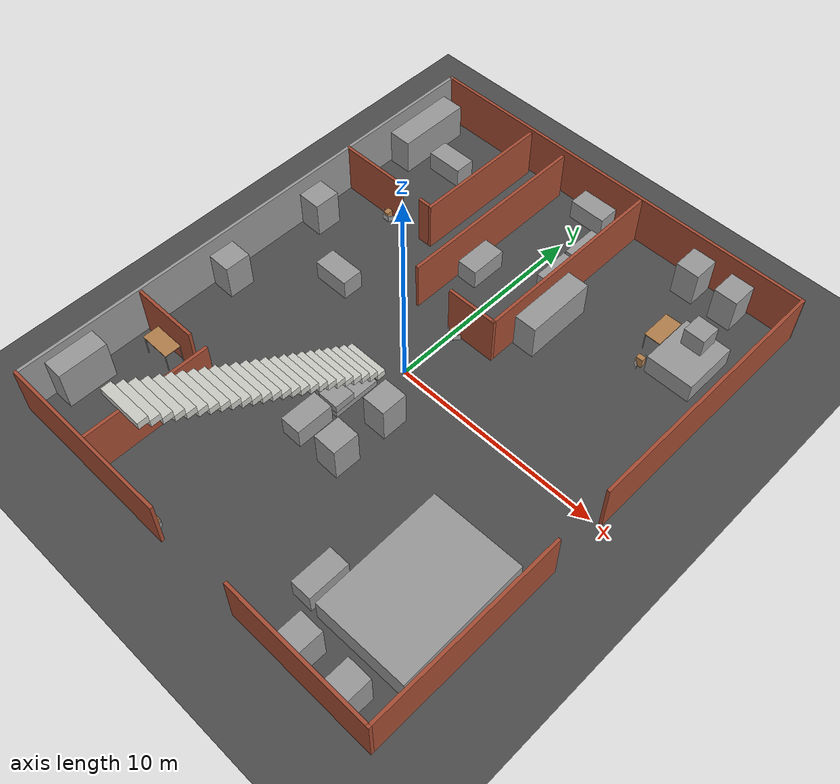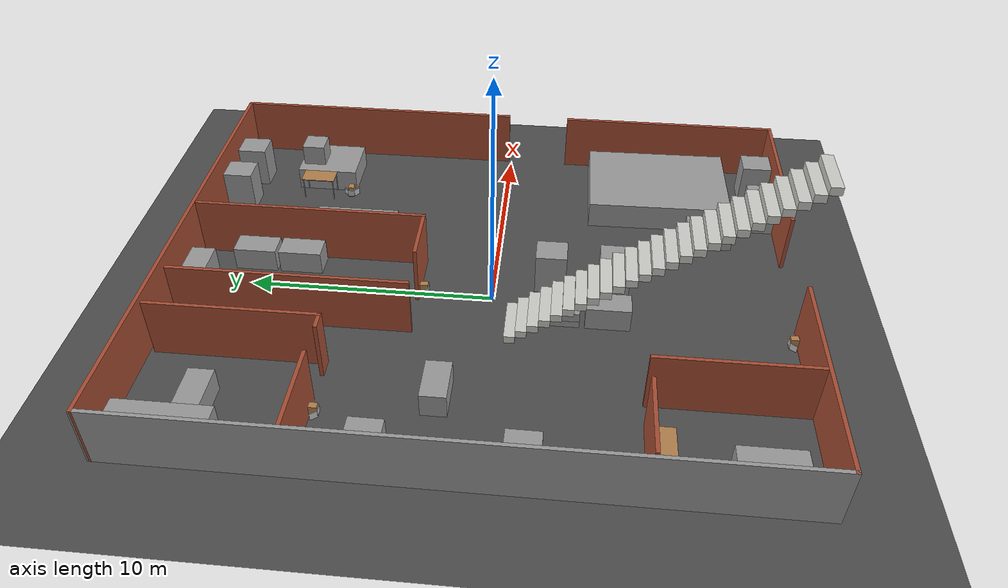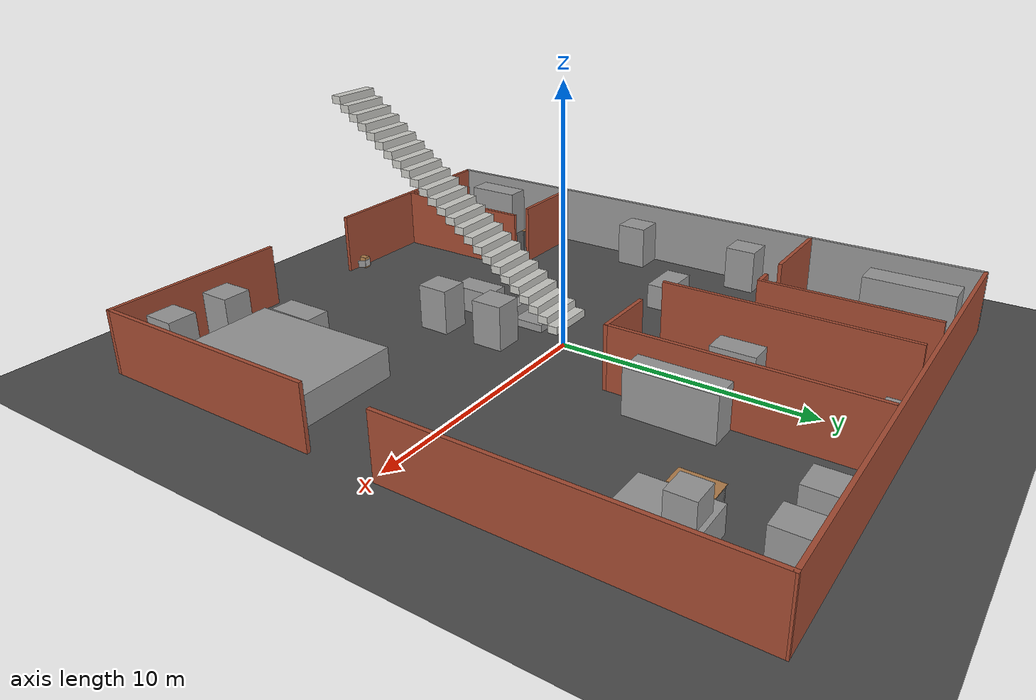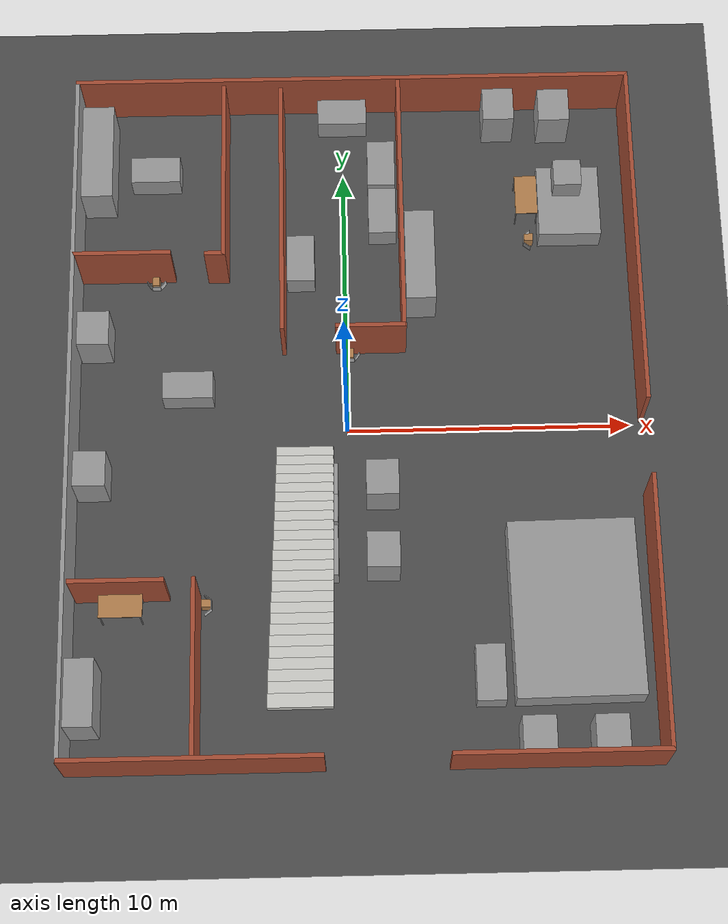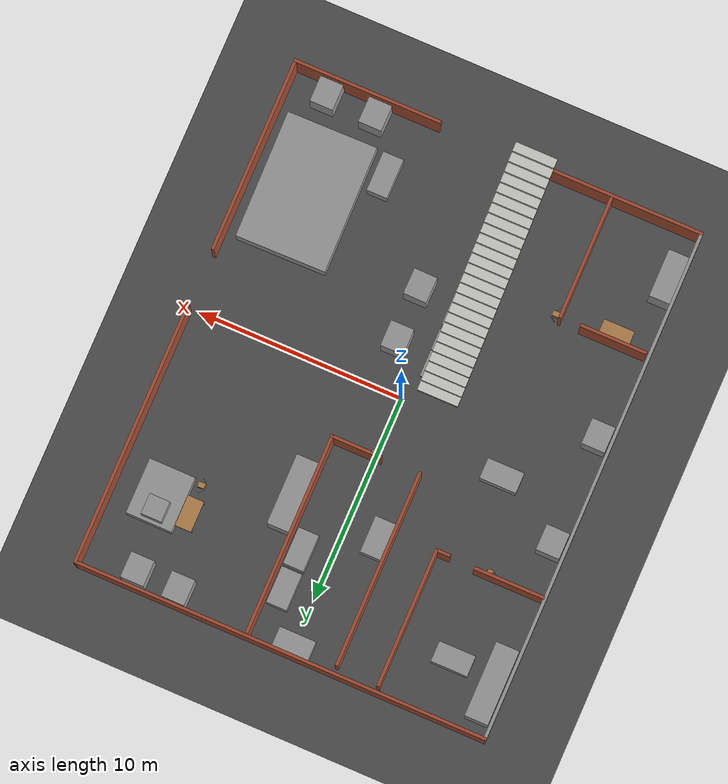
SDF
<sdf version="1.6">
 <world name="default">
  <light name="sun" type="directional">
   <pose>0 0 10 0 -0 0</pose>
   <diffuse>0.8 0.8 0.8 1</diffuse>
   <specular>0.2 0.2 0.2 1</specular>
   <attenuation>
    <range>1000</range>
    <constant>0.9</constant>
    <linear>0.01</linear>
    <quadratic>0.001</quadratic>
   </attenuation>
   <direction>-0.5 0.1 -0.9</direction>
  </light>
  <model name="ground_plane">
   <static>1</static>
   <link name="link">
    <collision name="collision">
     <geometry><plane><normal>0 0 1</normal><size>100 100</size></plane></geometry>
     <surface><friction><ode><mu>100</mu><mu2>50</mu2></ode></friction></surface>
    </collision>
    <visual name="visual">
     <cast_shadows>0</cast_shadows>
     <geometry><plane><normal>0 0 1</normal><size>100 100</size></plane></geometry>
     <material>
      <script><uri>file://media/materials/scripts/gazebo.material</uri><name>Gazebo/DarkGrey</name></script>
     </material>
    </visual>
   </link>
  </model>
  <gravity>0 0 -9.8</gravity>
  <magnetic_field>6e-06 2.3e-05 -4.2e-05</magnetic_field>
  <atmosphere type="adiabatic"/>
  <physics name="default_physics" default="0" type="ode">
   <max_step_size>0.001</max_step_size>
   <real_time_factor>1</real_time_factor>
   <real_time_update_rate>1000</real_time_update_rate>
  </physics>
  <scene><ambient>0.4 0.4 0.4 1</ambient><background>0.7 0.7 0.7 1</background><shadows>1</shadows></scene>
  <spherical_coordinates>
   <surface_model>EARTH_WGS84</surface_model>
   <latitude_deg>0</latitude_deg>
   <longitude_deg>0</longitude_deg>
   <elevation>0</elevation>
   <heading_deg>0</heading_deg>
  </spherical_coordinates>
  <model name="CIMA_LAB">
   <pose>0.392007 0.399325 0 0 -0 0</pose>
   <link name="Stairs_2">
    <visual name="Stairs_2_Visual_0">
     <pose>-1.90803 -1.27666 0.16 0 -0 0</pose>
     <geometry><box><size>2 0.44 0.32</size></box></geometry>
     <material>
      <script><uri>file://media/materials/scripts/gazebo.material</uri><name>Gazebo/CeilingTiled</name></script>
      <ambient>0.760784 0.662745 0.627451 1</ambient>
     </material>
     <meta><layer>0</layer></meta>
    </visual>
    <collision name="Stairs_2_Collision_0">
     <geometry><box><size>2 0.44 0.32</size></box></geometry>
     <pose>-1.90803 -1.27666 0.16 0 -0 0</pose>
    </collision>
    <visual name="Stairs_2_Visual_1">
     <pose>-1.90803 -1.71666 0.48 0 -0 0</pose>
     <geometry><box><size>2 0.44 0.32</size></box></geometry>
     <material>
      <script><uri>file://media/materials/scripts/gazebo.material</uri><name>Gazebo/CeilingTiled</name></script>
      <ambient>0.760784 0.662745 0.627451 1</ambient>
     </material>
     <meta><layer>0</layer></meta>
    </visual>
    <collision name="Stairs_2_Collision_1">
     <geometry><box><size>2 0.44 0.32</size></box></geometry>
     <pose>-1.90803 -1.71666 0.48 0 -0 0</pose>
    </collision>
    <visual name="Stairs_2_Visual_2">
     <pose>-1.90803 -2.15666 0.8 0 -0 0</pose>
     <geometry><box><size>2 0.44 0.32</size></box></geometry>
     <material>
      <script><uri>file://media/materials/scripts/gazebo.material</uri><name>Gazebo/CeilingTiled</name></script>
      <ambient>0.760784 0.662745 0.627451 1</ambient>
     </material>
     <meta><layer>0</layer></meta>
    </visual>
    <collision name="Stairs_2_Collision_2">
     <geometry><box><size>2 0.44 0.32</size></box></geometry>
     <pose>-1.90803 -2.15666 0.8 0 -0 0</pose>
    </collision>
    <visual name="Stairs_2_Visual_3">
     <pose>-1.90803 -2.59666 1.12 0 -0 0</pose>
     <geometry><box><size>2 0.44 0.32</size></box></geometry>
     <material>
      <script><uri>file://media/materials/scripts/gazebo.material</uri><name>Gazebo/CeilingTiled</name></script>
      <ambient>0.760784 0.662745 0.627451 1</ambient>
     </material>
     <meta><layer>0</layer></meta>
    </visual>
    <collision name="Stairs_2_Collision_3">
     <geometry><box><size>2 0.44 0.32</size></box></geometry>
     <pose>-1.90803 -2.59666 1.12 0 -0 0</pose>
    </collision>
    <visual name="Stairs_2_Visual_4">
     <pose>-1.90803 -3.03666 1.44 0 -0 0</pose>
     <geometry><box><size>2 0.44 0.32</size></box></geometry>
     <material>
      <script><uri>file://media/materials/scripts/gazebo.material</uri><name>Gazebo/CeilingTiled</name></script>
      <ambient>0.760784 0.662745 0.627451 1</ambient>
     </material>
     <meta><layer>0</layer></meta>
    </visual>
    <collision name="Stairs_2_Collision_4">
     <geometry><box><size>2 0.44 0.32</size></box></geometry>
     <pose>-1.90803 -3.03666 1.44 0 -0 0</pose>
    </collision>
    <visual name="Stairs_2_Visual_5">
     <pose>-1.90803 -3.47666 1.76 0 -0 0</pose>
     <geometry><box><size>2 0.44 0.32</size></box></geometry>
     <material>
      <script><uri>file://media/materials/scripts/gazebo.material</uri><name>Gazebo/CeilingTiled</name></script>
      <ambient>0.760784 0.662745 0.627451 1</ambient>
     </material>
     <meta><layer>0</layer></meta>
    </visual>
    <collision name="Stairs_2_Collision_5">
     <geometry><box><size>2 0.44 0.32</size></box></geometry>
     <pose>-1.90803 -3.47666 1.76 0 -0 0</pose>
    </collision>
    <visual name="Stairs_2_Visual_6">
     <pose>-1.90803 -3.91666 2.08 0 -0 0</pose>
     <geometry><box><size>2 0.44 0.32</size></box></geometry>
     <material>
      <script><uri>file://media/materials/scripts/gazebo.material</uri><name>Gazebo/CeilingTiled</name></script>
      <ambient>0.760784 0.662745 0.627451 1</ambient>
     </material>
     <meta><layer>0</layer></meta>
    </visual>
    <collision name="Stairs_2_Collision_6">
     <geometry><box><size>2 0.44 0.32</size></box></geometry>
     <pose>-1.90803 -3.91666 2.08 0 -0 0</pose>
    </collision>
    <visual name="Stairs_2_Visual_7">
     <pose>-1.90803 -4.35666 2.4 0 -0 0</pose>
     <geometry><box><size>2 0.44 0.32</size></box></geometry>
     <material>
      <script><uri>file://media/materials/scripts/gazebo.material</uri><name>Gazebo/CeilingTiled</name></script>
      <ambient>0.760784 0.662745 0.627451 1</ambient>
     </material>
     <meta><layer>0</layer></meta>
    </visual>
    <collision name="Stairs_2_Collision_7">
     <geometry><box><size>2 0.44 0.32</size></box></geometry>
     <pose>-1.90803 -4.35666 2.4 0 -0 0</pose>
    </collision>
    <visual name="Stairs_2_Visual_8">
     <pose>-1.90803 -4.79666 2.72 0 -0 0</pose>
     <geometry><box><size>2 0.44 0.32</size></box></geometry>
     <material>
      <script><uri>file://media/materials/scripts/gazebo.material</uri><name>Gazebo/CeilingTiled</name></script>
      <ambient>0.760784 0.662745 0.627451 1</ambient>
     </material>
     <meta><layer>0</layer></meta>
    </visual>
    <collision name="Stairs_2_Collision_8">
     <geometry><box><size>2 0.44 0.32</size></box></geometry>
     <pose>-1.90803 -4.79666 2.72 0 -0 0</pose>
    </collision>
    <visual name="Stairs_2_Visual_9">
     <pose>-1.90803 -5.23666 3.04 0 -0 0</pose>
     <geometry><box><size>2 0.44 0.32</size></box></geometry>
     <material>
      <script><uri>file://media/materials/scripts/gazebo.material</uri><name>Gazebo/CeilingTiled</name></script>
      <ambient>0.760784 0.662745 0.627451 1</ambient>
     </material>
     <meta><layer>0</layer></meta>
    </visual>
    <collision name="Stairs_2_Collision_9">
     <geometry><box><size>2 0.44 0.32</size></box></geometry>
     <pose>-1.90803 -5.23666 3.04 0 -0 0</pose>
    </collision>
    <visual name="Stairs_2_Visual_10">
     <pose>-1.90803 -5.67666 3.36 0 -0 0</pose>
     <geometry><box><size>2 0.44 0.32</size></box></geometry>
     <material>
      <script><uri>file://media/materials/scripts/gazebo.material</uri><name>Gazebo/CeilingTiled</name></script>
      <ambient>0.760784 0.662745 0.627451 1</ambient>
     </material>
     <meta><layer>0</layer></meta>
    </visual>
    <collision name="Stairs_2_Collision_10">
     <geometry><box><size>2 0.44 0.32</size></box></geometry>
     <pose>-1.90803 -5.67666 3.36 0 -0 0</pose>
    </collision>
    <visual name="Stairs_2_Visual_11">
     <pose>-1.90803 -6.11666 3.68 0 -0 0</pose>
     <geometry><box><size>2 0.44 0.32</size></box></geometry>
     <material>
      <script><uri>file://media/materials/scripts/gazebo.material</uri><name>Gazebo/CeilingTiled</name></script>
      <ambient>0.760784 0.662745 0.627451 1</ambient>
     </material>
     <meta><layer>0</layer></meta>
    </visual>
    <collision name="Stairs_2_Collision_11">
     <geometry><box><size>2 0.44 0.32</size></box></geometry>
     <pose>-1.90803 -6.11666 3.68 0 -0 0</pose>
    </collision>
    <visual name="Stairs_2_Visual_12">
     <pose>-1.90803 -6.55666 4 0 -0 0</pose>
     <geometry><box><size>2 0.44 0.32</size></box></geometry>
     <material>
      <script><uri>file://media/materials/scripts/gazebo.material</uri><name>Gazebo/CeilingTiled</name></script>
      <ambient>0.760784 0.662745 0.627451 1</ambient>
     </material>
     <meta><layer>0</layer></meta>
    </visual>
    <collision name="Stairs_2_Collision_12">
     <geometry><box><size>2 0.44 0.32</size></box></geometry>
     <pose>-1.90803 -6.55666 4 0 -0 0</pose>
    </collision>
    <visual name="Stairs_2_Visual_13">
     <pose>-1.90803 -6.99666 4.32 0 -0 0</pose>
     <geometry><box><size>2 0.44 0.32</size></box></geometry>
     <material>
      <script><uri>file://media/materials/scripts/gazebo.material</uri><name>Gazebo/CeilingTiled</name></script>
      <ambient>0.760784 0.662745 0.627451 1</ambient>
     </material>
     <meta><layer>0</layer></meta>
    </visual>
    <collision name="Stairs_2_Collision_13">
     <geometry><box><size>2 0.44 0.32</size></box></geometry>
     <pose>-1.90803 -6.99666 4.32 0 -0 0</pose>
    </collision>
    <visual name="Stairs_2_Visual_14">
     <pose>-1.90803 -7.43666 4.64 0 -0 0</pose>
     <geometry><box><size>2 0.44 0.32</size></box></geometry>
     <material>
      <script><uri>file://media/materials/scripts/gazebo.material</uri><name>Gazebo/CeilingTiled</name></script>
      <ambient>0.760784 0.662745 0.627451 1</ambient>
     </material>
     <meta><layer>0</layer></meta>
    </visual>
    <collision name="Stairs_2_Collision_14">
     <geometry><box><size>2 0.44 0.32</size></box></geometry>
     <pose>-1.90803 -7.43666 4.64 0 -0 0</pose>
    </collision>
    <visual name="Stairs_2_Visual_15">
     <pose>-1.90803 -7.87666 4.96 0 -0 0</pose>
     <geometry><box><size>2 0.44 0.32</size></box></geometry>
     <material>
      <script><uri>file://media/materials/scripts/gazebo.material</uri><name>Gazebo/CeilingTiled</name></script>
      <ambient>0.760784 0.662745 0.627451 1</ambient>
     </material>
     <meta><layer>0</layer></meta>
    </visual>
    <collision name="Stairs_2_Collision_15">
     <geometry><box><size>2 0.44 0.32</size></box></geometry>
     <pose>-1.90803 -7.87666 4.96 0 -0 0</pose>
    </collision>
    <visual name="Stairs_2_Visual_16">
     <pose>-1.90803 -8.31666 5.28 0 -0 0</pose>
     <geometry><box><size>2 0.44 0.32</size></box></geometry>
     <material>
      <script><uri>file://media/materials/scripts/gazebo.material</uri><name>Gazebo/CeilingTiled</name></script>
      <ambient>0.760784 0.662745 0.627451 1</ambient>
     </material>
     <meta><layer>0</layer></meta>
    </visual>
    <collision name="Stairs_2_Collision_16">
     <geometry><box><size>2 0.44 0.32</size></box></geometry>
     <pose>-1.90803 -8.31666 5.28 0 -0 0</pose>
    </collision>
    <visual name="Stairs_2_Visual_17">
     <pose>-1.90803 -8.75666 5.6 0 -0 0</pose>
     <geometry><box><size>2 0.44 0.32</size></box></geometry>
     <material>
      <script><uri>file://media/materials/scripts/gazebo.material</uri><name>Gazebo/CeilingTiled</name></script>
      <ambient>0.760784 0.662745 0.627451 1</ambient>
     </material>
     <meta><layer>0</layer></meta>
    </visual>
    <collision name="Stairs_2_Collision_17">
     <geometry><box><size>2 0.44 0.32</size></box></geometry>
     <pose>-1.90803 -8.75666 5.6 0 -0 0</pose>
    </collision>
    <visual name="Stairs_2_Visual_18">
     <pose>-1.90803 -9.19666 5.92 0 -0 0</pose>
     <geometry><box><size>2 0.44 0.32</size></box></geometry>
     <material>
      <script><uri>file://media/materials/scripts/gazebo.material</uri><name>Gazebo/CeilingTiled</name></script>
      <ambient>0.760784 0.662745 0.627451 1</ambient>
     </material>
     <meta><layer>0</layer></meta>
    </visual>
    <collision name="Stairs_2_Collision_18">
     <geometry><box><size>2 0.44 0.32</size></box></geometry>
     <pose>-1.90803 -9.19666 5.92 0 -0 0</pose>
    </collision>
    <visual name="Stairs_2_Visual_19">
     <pose>-1.90803 -9.63666 6.24 0 -0 0</pose>
     <geometry><box><size>2 0.44 0.32</size></box></geometry>
     <material>
      <script><uri>file://media/materials/scripts/gazebo.material</uri><name>Gazebo/CeilingTiled</name></script>
      <ambient>0.760784 0.662745 0.627451 1</ambient>
     </material>
     <meta><layer>0</layer></meta>
    </visual>
    <collision name="Stairs_2_Collision_19">
     <geometry><box><size>2 0.44 0.32</size></box></geometry>
     <pose>-1.90803 -9.63666 6.24 0 -0 0</pose>
    </collision>
    <visual name="Stairs_2_Visual_20">
     <pose>-1.90803 -10.0767 6.56 0 -0 0</pose>
     <geometry><box><size>2 0.44 0.32</size></box></geometry>
     <material>
      <script><uri>file://media/materials/scripts/gazebo.material</uri><name>Gazebo/CeilingTiled</name></script>
      <ambient>0.760784 0.662745 0.627451 1</ambient>
     </material>
     <meta><layer>0</layer></meta>
    </visual>
    <collision name="Stairs_2_Collision_20">
     <geometry><box><size>2 0.44 0.32</size></box></geometry>
     <pose>-1.90803 -10.0767 6.56 0 -0 0</pose>
    </collision>
    <visual name="Stairs_2_Visual_21">
     <pose>-1.90803 -10.5167 6.88 0 -0 0</pose>
     <geometry><box><size>2 0.44 0.32</size></box></geometry>
     <material>
      <script><uri>file://media/materials/scripts/gazebo.material</uri><name>Gazebo/CeilingTiled</name></script>
      <ambient>0.760784 0.662745 0.627451 1</ambient>
     </material>
     <meta><layer>0</layer></meta>
    </visual>
    <collision name="Stairs_2_Collision_21">
     <geometry><box><size>2 0.44 0.32</size></box></geometry>
     <pose>-1.90803 -10.5167 6.88 0 -0 0</pose>
    </collision>
    <visual name="Stairs_2_Visual_22">
     <pose>-1.90803 -10.9567 7.2 0 -0 0</pose>
     <geometry><box><size>2 0.44 0.32</size></box></geometry>
     <material>
      <script><uri>file://media/materials/scripts/gazebo.material</uri><name>Gazebo/CeilingTiled</name></script>
      <ambient>0.760784 0.662745 0.627451 1</ambient>
     </material>
     <meta><layer>0</layer></meta>
    </visual>
    <collision name="Stairs_2_Collision_22">
     <geometry><box><size>2 0.44 0.32</size></box></geometry>
     <pose>-1.90803 -10.9567 7.2 0 -0 0</pose>
    </collision>
    <visual name="Stairs_2_Visual_23">
     <pose>-1.90803 -11.3967 7.52 0 -0 0</pose>
     <geometry><box><size>2 0.44 0.32</size></box></geometry>
     <material>
      <script><uri>file://media/materials/scripts/gazebo.material</uri><name>Gazebo/CeilingTiled</name></script>
      <ambient>0.760784 0.662745 0.627451 1</ambient>
     </material>
     <meta><layer>0</layer></meta>
    </visual>
    <collision name="Stairs_2_Collision_23">
     <geometry><box><size>2 0.44 0.32</size></box></geometry>
     <pose>-1.90803 -11.3967 7.52 0 -0 0</pose>
    </collision>
    <visual name="Stairs_2_Visual_24">
     <pose>-1.90803 -11.8367 7.84 0 -0 0</pose>
     <geometry><box><size>2 0.44 0.32</size></box></geometry>
     <material>
      <script><uri>file://media/materials/scripts/gazebo.material</uri><name>Gazebo/CeilingTiled</name></script>
      <ambient>0.760784 0.662745 0.627451 1</ambient>
     </material>
     <meta><layer>0</layer></meta>
    </visual>
    <collision name="Stairs_2_Collision_24">
     <geometry><box><size>2 0.44 0.32</size></box></geometry>
     <pose>-1.90803 -11.8367 7.84 0 -0 0</pose>
    </collision>
   </link>
   <link name="Wall_0">
    <collision name="Wall_0_Collision">
     <geometry><box><size>25 0.15 2.5</size></box></geometry>
     <pose>0 0 1.25 0 -0 0</pose>
    </collision>
    <visual name="Wall_0_Visual">
     <pose>0 0 1.25 0 -0 0</pose>
     <geometry><box><size>25 0.15 2.5</size></box></geometry>
     <material>
      <script><uri>file://media/materials/scripts/gazebo.material</uri><name>Gazebo/Grey</name></script>
      <ambient>1 1 1 1</ambient>
     </material>
     <meta><layer>0</layer></meta>
    </visual>
    <pose>-10 0.009925 0 0 -0 -1.5708</pose>
   </link>
   <link name="Wall_15">
    <collision name="Wall_15_Collision">
     <geometry><box><size>0.75 0.15 2.5</size></box></geometry>
     <pose>0 0 1.25 0 -0 0</pose>
    </collision>
    <visual name="Wall_15_Visual">
     <pose>0 0 1.25 0 -0 0</pose>
     <geometry><box><size>0.75 0.15 2.5</size></box></geometry>
     <material>
      <script><uri>file://media/materials/scripts/gazebo.material</uri><name>Gazebo/Bricks</name></script>
      <ambient>1 1 1 1</ambient>
     </material>
     <meta><layer>0</layer></meta>
    </visual>
    <pose>-4.97494 5.50618 0 0 -0 0</pose>
   </link>
   <link name="Wall_16">
    <collision name="Wall_16_Collision">
     <geometry><box><size>6.75 0.15 2.5</size></box></geometry>
     <pose>0 0 1.25 0 -0 0</pose>
    </collision>
    <visual name="Wall_16_Visual">
     <pose>0 0 1.25 0 -0 0</pose>
     <geometry><box><size>6.75 0.15 2.5</size></box></geometry>
     <material>
      <script><uri>file://media/materials/scripts/gazebo.material</uri><name>Gazebo/Bricks</name></script>
      <ambient>1 1 1 1</ambient>
     </material>
     <meta><layer>0</layer></meta>
    </visual>
    <pose>-4.67494 8.80618 0 0 -0 1.5708</pose>
   </link>
   <link name="Wall_18">
    <collision name="Wall_18_Collision">
     <geometry><box><size>3.5 0.15 2.5</size></box></geometry>
     <pose>0 0 1.25 0 -0 0</pose>
    </collision>
    <visual name="Wall_18_Visual">
     <pose>0 0 1.25 0 -0 0</pose>
     <geometry><box><size>3.5 0.15 2.5</size></box></geometry>
     <material>
      <script><uri>file://media/materials/scripts/gazebo.material</uri><name>Gazebo/Bricks</name></script>
      <ambient>1 1 1 1</ambient>
     </material>
     <meta><layer>0</layer></meta>
    </visual>
    <pose>-8.28251 5.57631 0 0 -0 3.14159</pose>
   </link>
   <link name="Wall_2">
    <collision name="Wall_2_Collision">
     <geometry><box><size>12.75 0.15 2.5</size></box></geometry>
     <pose>0 0 1.25 0 -0 0</pose>
    </collision>
    <visual name="Wall_2_Visual">
     <pose>0 0 1.25 0 -0 0</pose>
     <geometry><box><size>12.75 0.15 2.5</size></box></geometry>
     <material>
      <script><uri>file://media/materials/scripts/gazebo.material</uri><name>Gazebo/Bricks</name></script>
      <ambient>1 1 1 1</ambient>
     </material>
     <meta><layer>0</layer></meta>
    </visual>
    <pose>10 6.09492 0 0 -0 1.5708</pose>
   </link>
   <link name="Wall_20">
    <collision name="Wall_20_Collision">
     <geometry><box><size>9.75 0.15 2.5</size></box></geometry>
     <pose>0 0 1.25 0 -0 0</pose>
    </collision>
    <visual name="Wall_20_Visual">
     <pose>0 0 1.25 0 -0 0</pose>
     <geometry><box><size>9.75 0.15 2.5</size></box></geometry>
     <material>
      <script><uri>file://media/materials/scripts/gazebo.material</uri><name>Gazebo/Bricks</name></script>
      <ambient>1 1 1 1</ambient>
     </material>
     <meta><layer>0</layer></meta>
    </visual>
    <pose>1.66843 7.43914 0 0 -0 -1.5708</pose>
   </link>
   <link name="Wall_21">
    <collision name="Wall_21_Collision">
     <geometry><box><size>2.5 0.15 2.5</size></box></geometry>
     <pose>0 0 1.25 0 -0 0</pose>
    </collision>
    <visual name="Wall_21_Visual">
     <pose>0 0 1.25 0 -0 0</pose>
     <geometry><box><size>2.5 0.15 2.5</size></box></geometry>
     <material>
      <script><uri>file://media/materials/scripts/gazebo.material</uri><name>Gazebo/Bricks</name></script>
      <ambient>1 1 1 1</ambient>
     </material>
     <meta><layer>0</layer></meta>
    </visual>
    <pose>0.493428 2.63914 0 0 -0 3.14159</pose>
   </link>
   <link name="Wall_23">
    <collision name="Wall_23_Collision">
     <geometry><box><size>9.5 0.15 2.5</size></box></geometry>
     <pose>0 0 1.25 0 -0 0</pose>
    </collision>
    <visual name="Wall_23_Visual">
     <pose>0 0 1.25 0 -0 0</pose>
     <geometry><box><size>9.5 0.15 2.5</size></box></geometry>
     <material>
      <script><uri>file://media/materials/scripts/gazebo.material</uri><name>Gazebo/Bricks</name></script>
      <ambient>1 1 1 1</ambient>
     </material>
     <meta><layer>0</layer></meta>
    </visual>
    <pose>-2.60981 7.30564 0 0 -0 1.5708</pose>
   </link>
   <link name="Wall_25">
    <collision name="Wall_25_Collision">
     <geometry><box><size>3.25 0.15 2.5</size></box></geometry>
     <pose>0 0 1.25 0 -0 0</pose>
    </collision>
    <visual name="Wall_25_Visual">
     <pose>0 0 1.25 0 -0 0</pose>
     <geometry><box><size>3.25 0.15 2.5</size></box></geometry>
     <material>
      <script><uri>file://media/materials/scripts/gazebo.material</uri><name>Gazebo/Bricks</name></script>
      <ambient>1 1 1 1</ambient>
     </material>
     <meta><layer>0</layer></meta>
    </visual>
    <pose>-8.22765 -6.41678 0 0 -0 3.14159</pose>
   </link>
   <link name="Wall_27">
    <collision name="Wall_27_Collision">
     <geometry><box><size>6 0.15 2.5</size></box></geometry>
     <pose>0 0 1.25 0 -0 0</pose>
    </collision>
    <visual name="Wall_27_Visual">
     <pose>0 0 1.25 0 -0 0</pose>
     <geometry><box><size>6 0.15 2.5</size></box></geometry>
     <material>
      <script><uri>file://media/materials/scripts/gazebo.material</uri><name>Gazebo/Bricks</name></script>
      <ambient>1 1 1 1</ambient>
     </material>
     <meta><layer>0</layer></meta>
    </visual>
    <pose>-5.62562 -9.34178 0 0 -0 -1.5708</pose>
   </link>
   <link name="Wall_3">
    <collision name="Wall_3_Collision">
     <geometry><box><size>20.15 0.15 2.5</size></box></geometry>
     <pose>0 0 1.25 0 -0 0</pose>
    </collision>
    <visual name="Wall_3_Visual">
     <pose>0 0 1.25 0 -0 0</pose>
     <geometry><box><size>20.15 0.15 2.5</size></box></geometry>
     <material>
      <script><uri>file://media/materials/scripts/gazebo.material</uri><name>Gazebo/Bricks</name></script>
      <ambient>1 1 1 1</ambient>
     </material>
     <meta><layer>0</layer></meta>
    </visual>
    <pose>0 12.4149 0 0 -0 3.13959</pose>
   </link>
   <link name="Wall_4">
    <collision name="Wall_4_Collision">
     <geometry><box><size>25 0.15 2.5</size></box></geometry>
     <pose>0 0 1.25 0 -0 0</pose>
    </collision>
    <visual name="Wall_4_Visual">
     <pose>0 0 1.25 0 -0 0</pose>
     <geometry><box><size>25 0.15 2.5</size></box></geometry>
     <material>
      <script><uri>file://media/materials/scripts/gazebo.material</uri><name>Gazebo/Bricks</name></script>
      <ambient>1 1 1 1</ambient>
     </material>
     <meta><layer>0</layer></meta>
    </visual>
    <pose>-10 0.009925 0 0 -0 -1.5708</pose>
   </link>
   <link name="Wall_5">
    <collision name="Wall_5_Collision">
     <geometry><box><size>8.75 0.15 2.5</size></box></geometry>
     <pose>0 0 1.25 0 -0 0</pose>
    </collision>
    <visual name="Wall_5_Visual">
     <pose>0 0 1.25 0 -0 0</pose>
     <geometry><box><size>8.75 0.15 2.5</size></box></geometry>
     <material>
      <script><uri>file://media/materials/scripts/gazebo.material</uri><name>Gazebo/Bricks</name></script>
      <ambient>1 1 1 1</ambient>
     </material>
     <meta><layer>0</layer></meta>
    </visual>
    <pose>-5.7 -12.4151 0 0 -0 0</pose>
   </link>
   <link name="Wall_7">
    <collision name="Wall_7_Collision">
     <geometry><box><size>9.5 0.15 2.5</size></box></geometry>
     <pose>0 0 1.25 0 -0 0</pose>
    </collision>
    <visual name="Wall_7_Visual">
     <pose>0 0 1.25 0 -0 0</pose>
     <geometry><box><size>9.5 0.15 2.5</size></box></geometry>
     <material>
      <script><uri>file://media/materials/scripts/gazebo.material</uri><name>Gazebo/Bricks</name></script>
      <ambient>1 1 1 1</ambient>
     </material>
     <meta><layer>0</layer></meta>
    </visual>
    <pose>10 -7.76007 0 0 -0 -1.5708</pose>
   </link>
   <link name="Wall_8">
    <collision name="Wall_8_Collision">
     <geometry><box><size>7.25 0.15 2.5</size></box></geometry>
     <pose>0 0 1.25 0 -0 0</pose>
    </collision>
    <visual name="Wall_8_Visual">
     <pose>0 0 1.25 0 -0 0</pose>
     <geometry><box><size>7.25 0.15 2.5</size></box></geometry>
     <material>
      <script><uri>file://media/materials/scripts/gazebo.material</uri><name>Gazebo/Bricks</name></script>
      <ambient>1 1 1 1</ambient>
     </material>
     <meta><layer>0</layer></meta>
    </visual>
    <pose>6.45 -12.4351 0 0 -0 3.14159</pose>
   </link>
   <static>1</static>
  </model>
  <model name="unit_box_clone">
   <pose>1.15733 -4.90091 0.892855 0 0 -0.012171</pose>
   <link name="link">
    <inertial>
     <mass>1</mass>
     <inertia>
      <ixx>0.166667</ixx>
      <ixy>0</ixy>
      <ixz>0</ixz>
      <iyy>0.166667</iyy>
      <iyz>0</iyz>
      <izz>0.166667</izz>
     </inertia>
    </inertial>
    <collision name="collision"><geometry><box><size>1.13282 1.25934 1.78571</size></box></geometry></collision>
    <visual name="visual">
     <geometry><box><size>1.13282 1.25934 1.78571</size></box></geometry>
     <material>
      <script><name>Gazebo/Grey</name><uri>file://media/materials/scripts/gazebo.material</uri></script>
     </material>
    </visual>
   </link>
  </model>
  <model name="unit_box_clone_0">
   <pose>5.73018 12.0225 0.892855 0 0 -0.002519</pose>
   <link name="link">
    <inertial>
     <mass>1</mass>
     <inertia>
      <ixx>0.166667</ixx>
      <ixy>0</ixy>
      <ixz>0</ixz>
      <iyy>0.166667</iyy>
      <iyz>0</iyz>
      <izz>0.166667</izz>
     </inertia>
    </inertial>
    <collision name="collision"><geometry><box><size>1.13282 1.25934 1.78571</size></box></geometry></collision>
    <visual name="visual">
     <geometry><box><size>1.13282 1.25934 1.78571</size></box></geometry>
     <material>
      <script><name>Gazebo/Grey</name><uri>file://media/materials/scripts/gazebo.material</uri></script>
     </material>
    </visual>
   </link>
  </model>
  <model name="unit_box_clone_1">
   <pose>7.76064 11.9532 0.892855 -0 -0 -0.00242</pose>
   <link name="link">
    <inertial>
     <mass>1</mass>
     <inertia>
      <ixx>0.166667</ixx>
      <ixy>0</ixy>
      <ixz>0</ixz>
      <iyy>0.166667</iyy>
      <iyz>0</iyz>
      <izz>0.166667</izz>
     </inertia>
    </inertial>
    <collision name="collision"><geometry><box><size>1.13282 1.25934 1.78571</size></box></geometry></collision>
    <visual name="visual">
     <geometry><box><size>1.13282 1.25934 1.78571</size></box></geometry>
     <material>
      <script><name>Gazebo/Grey</name><uri>file://media/materials/scripts/gazebo.material</uri></script>
     </material>
    </visual>
   </link>
  </model>
  <model name="unit_box_clone_3">
   <pose>8.55641 -11.3311 0.892851 6e-06 -1e-06 -3e-06</pose>
   <link name="link">
    <inertial>
     <mass>1</mass>
     <inertia>
      <ixx>0.166667</ixx>
      <ixy>0</ixy>
      <ixz>0</ixz>
      <iyy>0.166667</iyy>
      <iyz>0</iyz>
      <izz>0.166667</izz>
     </inertia>
    </inertial>
    <collision name="collision"><geometry><box><size>1.13282 1.25934 1.78571</size></box></geometry></collision>
    <visual name="visual">
     <geometry><box><size>1.13282 1.25934 1.78571</size></box></geometry>
     <material>
      <script><name>Gazebo/Grey</name><uri>file://media/materials/scripts/gazebo.material</uri></script>
     </material>
    </visual>
   </link>
  </model>
  <model name="unit_box_clone_4">
   <pose>6.15028 -11.3248 0.892851 6e-06 0 -0.004505</pose>
   <link name="link">
    <inertial>
     <mass>1</mass>
     <inertia>
      <ixx>0.166667</ixx>
      <ixy>0</ixy>
      <ixz>0</ixz>
      <iyy>0.166667</iyy>
      <iyz>0</iyz>
      <izz>0.166667</izz>
     </inertia>
    </inertial>
    <collision name="collision"><geometry><box><size>1.13282 1.25934 1.78571</size></box></geometry></collision>
    <visual name="visual">
     <geometry><box><size>1.13282 1.25934 1.78571</size></box></geometry>
     <material>
      <script><name>Gazebo/Grey</name><uri>file://media/materials/scripts/gazebo.material</uri></script>
     </material>
    </visual>
   </link>
  </model>
  <model name="unit_box_1_clone">
   <pose>-5.61874 1.50263 0.499995 -2e-06 6e-06 1.5708</pose>
   <link name="link">
    <inertial>
     <mass>1</mass>
     <inertia>
      <ixx>0.166667</ixx>
      <ixy>0</ixy>
      <ixz>0</ixz>
      <iyy>0.166667</iyy>
      <iyz>0</iyz>
      <izz>0.166667</izz>
     </inertia>
    </inertial>
    <collision name="collision"><geometry><box><size>1 1.78009 1</size></box></geometry></collision>
    <visual name="visual">
     <geometry><box><size>1 1.78009 1</size></box></geometry>
     <material>
      <script><name>Gazebo/Grey</name><uri>file://media/materials/scripts/gazebo.material</uri></script>
     </material>
    </visual>
   </link>
  </model>
  <model name="unit_box_clone_5">
   <pose>-8.91772 3.42618 0.892851 6e-06 -0 -0.00583</pose>
   <link name="link">
    <inertial>
     <mass>1</mass>
     <inertia>
      <ixx>0.166667</ixx>
      <ixy>0</ixy>
      <ixz>0</ixz>
      <iyy>0.166667</iyy>
      <iyz>0</iyz>
      <izz>0.166667</izz>
     </inertia>
    </inertial>
    <collision name="collision"><geometry><box><size>1.13282 1.25934 1.78571</size></box></geometry></collision>
    <visual name="visual">
     <geometry><box><size>1.13282 1.25934 1.78571</size></box></geometry>
     <material>
      <script><name>Gazebo/Grey</name><uri>file://media/materials/scripts/gazebo.material</uri></script>
     </material>
    </visual>
   </link>
  </model>
  <model name="unit_box_clone_6">
   <pose>-8.91775 -1.81085 0.892855 0 0 -0.008855</pose>
   <link name="link">
    <inertial>
     <mass>1</mass>
     <inertia>
      <ixx>0.166667</ixx>
      <ixy>0</ixy>
      <ixz>0</ixz>
      <iyy>0.166667</iyy>
      <iyz>0</iyz>
      <izz>0.166667</izz>
     </inertia>
    </inertial>
    <collision name="collision"><geometry><box><size>1.13282 1.25934 1.78571</size></box></geometry></collision>
    <visual name="visual">
     <geometry><box><size>1.13282 1.25934 1.78571</size></box></geometry>
     <material>
      <script><name>Gazebo/Grey</name><uri>file://media/materials/scripts/gazebo.material</uri></script>
     </material>
    </visual>
   </link>
  </model>
  <model name="unit_box_1_clone_clone">
   <pose>-6.86867 9.99177 0.5 0 -0 1.57082</pose>
   <link name="link">
    <inertial>
     <mass>1</mass>
     <inertia>
      <ixx>0.166667</ixx>
      <ixy>0</ixy>
      <ixz>0</ixz>
      <iyy>0.166667</iyy>
      <iyz>0</iyz>
      <izz>0.166667</izz>
     </inertia>
    </inertial>
    <collision name="collision"><geometry><box><size>1 1.78009 1</size></box></geometry></collision>
    <visual name="visual">
     <geometry><box><size>1 1.78009 1</size></box></geometry>
     <material>
      <script><name>Gazebo/Grey</name><uri>file://media/materials/scripts/gazebo.material</uri></script>
     </material>
    </visual>
   </link>
  </model>
  <model name="unit_box_clone_2_clone">
   <pose>-8.91755 10.3807 0.892637 -0.00012 -0 1.2e-05</pose>
   <link name="link">
    <inertial>
     <mass>1</mass>
     <inertia>
      <ixx>0.166667</ixx>
      <ixy>0</ixy>
      <ixz>0</ixz>
      <iyy>0.166667</iyy>
      <iyz>0</iyz>
      <izz>0.166667</izz>
     </inertia>
    </inertial>
    <collision name="collision"><geometry><box><size>1.13282 3.62061 1.78571</size></box></geometry></collision>
    <visual name="visual">
     <geometry><box><size>1.13282 3.62061 1.78571</size></box></geometry>
     <material>
      <script><name>Gazebo/Grey</name><uri>file://media/materials/scripts/gazebo.material</uri></script>
     </material>
    </visual>
   </link>
  </model>
  <model name="unit_box_1_clone_clone_0">
   <pose>-0.008701 12.2398 0.5 0 -0 1.56888</pose>
   <link name="link">
    <inertial>
     <mass>1</mass>
     <inertia>
      <ixx>0.166667</ixx>
      <ixy>0</ixy>
      <ixz>0</ixz>
      <iyy>0.166667</iyy>
      <iyz>0</iyz>
      <izz>0.166667</izz>
     </inertia>
    </inertial>
    <collision name="collision"><geometry><box><size>1 1.78009 1</size></box></geometry></collision>
    <visual name="visual">
     <geometry><box><size>1 1.78009 1</size></box></geometry>
     <material>
      <script><name>Gazebo/Grey</name><uri>file://media/materials/scripts/gazebo.material</uri></script>
     </material>
    </visual>
   </link>
  </model>
  <model name="unit_box_1_clone_clone_1">
   <pose>-1.59397 6.32067 0.5 0 -0 -3.14157</pose>
   <link name="link">
    <inertial>
     <mass>1</mass>
     <inertia>
      <ixx>0.166667</ixx>
      <ixy>0</ixy>
      <ixz>0</ixz>
      <iyy>0.166667</iyy>
      <iyz>0</iyz>
      <izz>0.166667</izz>
     </inertia>
    </inertial>
    <collision name="collision"><geometry><box><size>1 1.78009 1</size></box></geometry></collision>
    <visual name="visual">
     <geometry><box><size>1 1.78009 1</size></box></geometry>
     <material>
      <script><name>Gazebo/Grey</name><uri>file://media/materials/scripts/gazebo.material</uri></script>
     </material>
    </visual>
   </link>
  </model>
  <model name="unit_box_1_clone_clone_2">
   <pose>1.39031 8.16896 0.5 0 -0 3.14142</pose>
   <link name="link">
    <inertial>
     <mass>1</mass>
     <inertia>
      <ixx>0.166667</ixx>
      <ixy>0</ixy>
      <ixz>0</ixz>
      <iyy>0.166667</iyy>
      <iyz>0</iyz>
      <izz>0.166667</izz>
     </inertia>
    </inertial>
    <collision name="collision"><geometry><box><size>1 1.78009 1</size></box></geometry></collision>
    <visual name="visual">
     <geometry><box><size>1 1.78009 1</size></box></geometry>
     <material>
      <script><name>Gazebo/Grey</name><uri>file://media/materials/scripts/gazebo.material</uri></script>
     </material>
    </visual>
   </link>
  </model>
  <model name="unit_box_1_clone_clone_2_clone">
   <pose>1.39025 10.0864 0.499995 -0 9e-06 3.14131</pose>
   <link name="link">
    <inertial>
     <mass>1</mass>
     <inertia>
      <ixx>0.166667</ixx>
      <ixy>0</ixy>
      <ixz>0</ixz>
      <iyy>0.166667</iyy>
      <iyz>0</iyz>
      <izz>0.166667</izz>
     </inertia>
    </inertial>
    <collision name="collision"><geometry><box><size>1 1.78009 1</size></box></geometry></collision>
    <visual name="visual">
     <geometry><box><size>1 1.78009 1</size></box></geometry>
     <material>
      <script><name>Gazebo/Grey</name><uri>file://media/materials/scripts/gazebo.material</uri></script>
     </material>
    </visual>
   </link>
  </model>
  <model name="unit_box_1_clone_0">
   <pose>-0.888348 -4.66798 0.499995 0 9e-06 1.4e-05</pose>
   <link name="link">
    <inertial>
     <mass>1</mass>
     <inertia>
      <ixx>0.166667</ixx>
      <ixy>0</ixy>
      <ixz>0</ixz>
      <iyy>0.166667</iyy>
      <iyz>0</iyz>
      <izz>0.166667</izz>
     </inertia>
    </inertial>
    <collision name="collision"><geometry><box><size>1 1.78009 1</size></box></geometry></collision>
    <visual name="visual">
     <geometry><box><size>1 1.78009 1</size></box></geometry>
     <material>
      <script><name>Gazebo/Grey</name><uri>file://media/materials/scripts/gazebo.material</uri></script>
     </material>
    </visual>
   </link>
  </model>
  <audio><device>default</device></audio>
  <model name="unit_box_1_clone_clone_2_clone_0">
   <link name="link">
    <inertial>
     <mass>1</mass>
     <inertia>
      <ixx>0.166667</ixx>
      <ixy>0</ixy>
      <ixz>0</ixz>
      <iyy>0.166667</iyy>
      <iyz>0</iyz>
      <izz>0.166667</izz>
     </inertia>
    </inertial>
    <visual name="visual">
     <geometry><box><size>2.24701 2.69579 1</size></box></geometry>
     <material>
      <script><name>Gazebo/Grey</name><uri>file://media/materials/scripts/gazebo.material</uri></script>
      <emissive>0 0 0 1</emissive>
     </material>
    </visual>
    <collision name="collision">
     <geometry><box><size>2.24701 2.69579 1</size></box></geometry>
     <surface>
      <friction>
       <ode><mu>1</mu><mu2>1</mu2><fdir1>0 0 0</fdir1><slip1>0</slip1><slip2>0</slip2></ode>
       <torsional>
        <coefficient>1</coefficient>
        <patch_radius>0</patch_radius>
        <surface_radius>0</surface_radius>
        <use_patch_radius>1</use_patch_radius>
        <ode><slip>0</slip></ode>
       </torsional>
      </friction>
      <bounce><restitution_coefficient>0</restitution_coefficient><threshold>1e+06</threshold></bounce>
      <contact>
       <collide_without_contact>0</collide_without_contact>
       <collide_without_contact_bitmask>1</collide_without_contact_bitmask>
       <collide_bitmask>1</collide_bitmask>
       <ode>
        <soft_cfm>0</soft_cfm>
        <soft_erp>0.2</soft_erp>
        <kp>1e+13</kp>
        <kd>1</kd>
        <max_vel>0.01</max_vel>
        <min_depth>0</min_depth>
       </ode>
       <bullet>
        <split_impulse>1</split_impulse>
        <split_impulse_penetration_threshold>-0.01</split_impulse_penetration_threshold>
        <soft_cfm>0</soft_cfm>
        <soft_erp>0.2</soft_erp>
        <kp>1e+13</kp>
        <kd>1</kd>
       </bullet>
      </contact>
     </surface>
    </collision>
   </link>
   <link name="link_0">
    <inertial>
     <mass>1</mass>
     <inertia>
      <ixx>0.166667</ixx>
      <ixy>0</ixy>
      <ixz>0</ixz>
      <iyy>0.166667</iyy>
      <iyz>0</iyz>
      <izz>0.166667</izz>
     </inertia>
    </inertial>
    <pose>0.087398 -0.681979 0.921931 0 -2.9e-05 3.1398</pose>
    <visual name="visual">
     <geometry><box><size>1 1 1</size></box></geometry>
     <material>
      <lighting>1</lighting>
      <script><uri>file://media/materials/scripts/gazebo.material</uri><name>Gazebo/Grey</name></script>
      <emissive>0 0 0 1</emissive>
     </material>
    </visual>
    <collision name="collision">
     <geometry><box><size>1 1 1</size></box></geometry>
     <surface>
      <friction>
       <ode><mu>1</mu><mu2>1</mu2><fdir1>0 0 0</fdir1><slip1>0</slip1><slip2>0</slip2></ode>
       <torsional>
        <coefficient>1</coefficient>
        <patch_radius>0</patch_radius>
        <surface_radius>0</surface_radius>
        <use_patch_radius>1</use_patch_radius>
        <ode><slip>0</slip></ode>
       </torsional>
      </friction>
      <bounce><restitution_coefficient>0</restitution_coefficient><threshold>1e+06</threshold></bounce>
      <contact>
       <collide_without_contact>0</collide_without_contact>
       <collide_without_contact_bitmask>1</collide_without_contact_bitmask>
       <collide_bitmask>1</collide_bitmask>
       <ode>
        <soft_cfm>0</soft_cfm>
        <soft_erp>0.2</soft_erp>
        <kp>1e+13</kp>
        <kd>1</kd>
        <max_vel>0.01</max_vel>
        <min_depth>0</min_depth>
       </ode>
       <bullet>
        <split_impulse>1</split_impulse>
        <split_impulse_penetration_threshold>-0.01</split_impulse_penetration_threshold>
        <soft_cfm>0</soft_cfm>
        <soft_erp>0.2</soft_erp>
        <kp>1e+13</kp>
        <kd>1</kd>
       </bullet>
      </contact>
     </surface>
    </collision>
   </link>
   <joint name="link_JOINT_0" type="fixed">
    <parent>link</parent>
    <child>link_0</child>
    <physics>
     <ode><limit><cfm>0</cfm><erp>0.2</erp></limit><suspension><cfm>0</cfm><erp>0.2</erp></suspension></ode>
    </physics>
   </joint>
   <static>0</static>
   <pose>8.1952 8.42159 0.499996 0 -3e-06 3.13985</pose>
  </model>
  <model name="Support_box_wood">
   <link name="link">
    <inertial>
     <mass>0.0406949</mass>
     <inertia>
      <ixx>0.00114102</ixx>
      <ixy>0</ixy>
      <ixz>0</ixz>
      <iyy>0.00102768</iyy>
      <iyz>0</iyz>
      <izz>0.000581951</izz>
     </inertia>
    </inertial>
    <pose>0.062754 0.860403 -0.243846 0 -0 0</pose>
    <visual name="visual">
     <geometry><box><size>0.252854 0.320175 0.483682</size></box></geometry>
     <material>
      <script><name>Gazebo/Wood</name><uri>file://media/materials/scripts/gazebo.material</uri></script>
      <shader type="vertex"><normal_map>__default__</normal_map></shader>
      <ambient>0.3 0.3 0.3 1</ambient>
      <diffuse>0.7 0.7 0.7 1</diffuse>
      <specular>0.01 0.01 0.01 1</specular>
      <emissive>0 0 0 1</emissive>
     </material>
    </visual>
    <visual name="ModelPreview_4::link::visual_1">
     <geometry><box><size>0.252854 0.320175 0.483682</size></box></geometry>
     <material>
      <script><name>Gazebo/Wood</name><uri>file://media/materials/scripts/gazebo.material</uri></script>
      <shader type="vertex"><normal_map>__default__</normal_map></shader>
      <ambient>0.3 0.3 0.3 1</ambient>
      <diffuse>0.7 0.7 0.7 1</diffuse>
      <specular>0.01 0.01 0.01 1</specular>
      <emissive>0 0 0 1</emissive>
     </material>
    </visual>
    <collision name="collision">
     <geometry><box><size>0.262854 0.320175 0.483683</size></box></geometry>
     <surface>
      <friction>
       <ode><mu>1</mu><mu2>1</mu2><fdir1>0 0 0</fdir1><slip1>0</slip1><slip2>0</slip2></ode>
       <torsional>
        <coefficient>1</coefficient>
        <patch_radius>0</patch_radius>
        <surface_radius>0</surface_radius>
        <use_patch_radius>1</use_patch_radius>
        <ode><slip>0</slip></ode>
       </torsional>
      </friction>
      <bounce><restitution_coefficient>0</restitution_coefficient><threshold>1e+06</threshold></bounce>
      <contact>
       <collide_without_contact>0</collide_without_contact>
       <collide_without_contact_bitmask>1</collide_without_contact_bitmask>
       <collide_bitmask>1</collide_bitmask>
       <ode>
        <soft_cfm>0</soft_cfm>
        <soft_erp>0.2</soft_erp>
        <kp>1e+13</kp>
        <kd>1</kd>
        <max_vel>0.01</max_vel>
        <min_depth>0</min_depth>
       </ode>
       <bullet>
        <split_impulse>1</split_impulse>
        <split_impulse_penetration_threshold>-0.01</split_impulse_penetration_threshold>
        <soft_cfm>0</soft_cfm>
        <soft_erp>0.2</soft_erp>
        <kp>1e+13</kp>
        <kd>1</kd>
       </bullet>
      </contact>
     </surface>
    </collision>
   </link>
   <static>0</static>
   <pose>0.062709 1.94294 0.485697 -1.4e-05 -0 0.000215</pose>
  </model>
  <model name="Support_box_wood_clone">
   <link name="link">
    <inertial>
     <mass>0.0406949</mass>
     <inertia>
      <ixx>0.00114102</ixx>
      <ixy>0</ixy>
      <ixz>0</ixz>
      <iyy>0.00102768</iyy>
      <iyz>0</iyz>
      <izz>0.000581951</izz>
     </inertia>
    </inertial>
    <pose>0.062754 0.860403 -0.243846 0 -0 0</pose>
    <visual name="visual">
     <geometry><box><size>0.252854 0.320175 0.483682</size></box></geometry>
     <material>
      <script><name>Gazebo/Wood</name><uri>file://media/materials/scripts/gazebo.material</uri></script>
      <shader type="vertex"><normal_map>__default__</normal_map></shader>
      <ambient>0.3 0.3 0.3 1</ambient>
      <diffuse>0.7 0.7 0.7 1</diffuse>
      <specular>0.01 0.01 0.01 1</specular>
      <emissive>0 0 0 1</emissive>
     </material>
    </visual>
    <visual name="ModelPreview_4::link::visual_1">
     <geometry><box><size>0.252854 0.320175 0.483682</size></box></geometry>
     <material>
      <script><name>Gazebo/Wood</name><uri>file://media/materials/scripts/gazebo.material</uri></script>
      <shader type="vertex"><normal_map>__default__</normal_map></shader>
      <ambient>0.3 0.3 0.3 1</ambient>
      <diffuse>0.7 0.7 0.7 1</diffuse>
      <specular>0.01 0.01 0.01 1</specular>
      <emissive>0 0 0 1</emissive>
     </material>
    </visual>
    <collision name="collision">
     <geometry><box><size>0.262854 0.320175 0.483683</size></box></geometry>
     <surface>
      <friction>
       <ode><mu>1</mu><mu2>1</mu2><fdir1>0 0 0</fdir1><slip1>0</slip1><slip2>0</slip2></ode>
       <torsional>
        <coefficient>1</coefficient>
        <patch_radius>0</patch_radius>
        <surface_radius>0</surface_radius>
        <use_patch_radius>1</use_patch_radius>
        <ode><slip>0</slip></ode>
       </torsional>
      </friction>
      <bounce><restitution_coefficient>0</restitution_coefficient><threshold>1e+06</threshold></bounce>
      <contact>
       <collide_without_contact>0</collide_without_contact>
       <collide_without_contact_bitmask>1</collide_without_contact_bitmask>
       <collide_bitmask>1</collide_bitmask>
       <ode>
        <soft_cfm>0</soft_cfm>
        <soft_erp>0.2</soft_erp>
        <kp>1e+13</kp>
        <kd>1</kd>
        <max_vel>0.01</max_vel>
        <min_depth>0</min_depth>
       </ode>
       <bullet>
        <split_impulse>1</split_impulse>
        <split_impulse_penetration_threshold>-0.01</split_impulse_penetration_threshold>
        <soft_cfm>0</soft_cfm>
        <soft_erp>0.2</soft_erp>
        <kp>1e+13</kp>
        <kd>1</kd>
       </bullet>
      </contact>
     </surface>
    </collision>
   </link>
   <static>0</static>
   <pose>-6.90157 4.8801 0.485687 0 -0 0.000178</pose>
  </model>
  <model name="Support_box_wood_clone_clone">
   <link name="link">
    <inertial>
     <mass>0.0406949</mass>
     <inertia>
      <ixx>0.00114102</ixx>
      <ixy>0</ixy>
      <ixz>0</ixz>
      <iyy>0.00102768</iyy>
      <iyz>0</iyz>
      <izz>0.000581951</izz>
     </inertia>
    </inertial>
    <pose>0.062754 0.860403 -0.243846 0 -0 0</pose>
    <visual name="visual">
     <geometry><box><size>0.252854 0.320175 0.483682</size></box></geometry>
     <material>
      <script><name>Gazebo/Wood</name><uri>file://media/materials/scripts/gazebo.material</uri></script>
      <shader type="vertex"><normal_map>__default__</normal_map></shader>
      <ambient>0.3 0.3 0.3 1</ambient>
      <diffuse>0.7 0.7 0.7 1</diffuse>
      <specular>0.01 0.01 0.01 1</specular>
      <emissive>0 0 0 1</emissive>
     </material>
    </visual>
    <visual name="ModelPreview_4::link::visual_1">
     <geometry><box><size>0.252854 0.320175 0.483682</size></box></geometry>
     <material>
      <script><name>Gazebo/Wood</name><uri>file://media/materials/scripts/gazebo.material</uri></script>
      <shader type="vertex"><normal_map>__default__</normal_map></shader>
      <ambient>0.3 0.3 0.3 1</ambient>
      <diffuse>0.7 0.7 0.7 1</diffuse>
      <specular>0.01 0.01 0.01 1</specular>
      <emissive>0 0 0 1</emissive>
     </material>
    </visual>
    <collision name="collision">
     <geometry><box><size>0.262854 0.320175 0.483683</size></box></geometry>
     <surface>
      <friction>
       <ode><mu>1</mu><mu2>1</mu2><fdir1>0 0 0</fdir1><slip1>0</slip1><slip2>0</slip2></ode>
       <torsional>
        <coefficient>1</coefficient>
        <patch_radius>0</patch_radius>
        <surface_radius>0</surface_radius>
        <use_patch_radius>1</use_patch_radius>
        <ode><slip>0</slip></ode>
       </torsional>
      </friction>
      <bounce><restitution_coefficient>0</restitution_coefficient><threshold>1e+06</threshold></bounce>
      <contact>
       <collide_without_contact>0</collide_without_contact>
       <collide_without_contact_bitmask>1</collide_without_contact_bitmask>
       <collide_bitmask>1</collide_bitmask>
       <ode>
        <soft_cfm>0</soft_cfm>
        <soft_erp>0.2</soft_erp>
        <kp>1e+13</kp>
        <kd>1</kd>
        <max_vel>0.01</max_vel>
        <min_depth>0</min_depth>
       </ode>
       <bullet>
        <split_impulse>1</split_impulse>
        <split_impulse_penetration_threshold>-0.01</split_impulse_penetration_threshold>
        <soft_cfm>0</soft_cfm>
        <soft_erp>0.2</soft_erp>
        <kp>1e+13</kp>
        <kd>1</kd>
       </bullet>
      </contact>
     </surface>
    </collision>
   </link>
   <static>0</static>
   <pose>-5.81113 -6.22506 0.48567 1.7e-05 1e-05 -1.6089</pose>
  </model>
  <model name="Support_box_wood_clone_clone_clone">
   <link name="link">
    <inertial>
     <mass>0.0406949</mass>
     <inertia>
      <ixx>0.00114102</ixx>
      <ixy>0</ixy>
      <ixz>0</ixz>
      <iyy>0.00102768</iyy>
      <iyz>0</iyz>
      <izz>0.000581951</izz>
     </inertia>
    </inertial>
    <pose>0.062754 0.860403 -0.243846 0 -0 0</pose>
    <visual name="visual">
     <geometry><box><size>0.252854 0.320175 0.483682</size></box></geometry>
     <material>
      <script><name>Gazebo/Wood</name><uri>file://media/materials/scripts/gazebo.material</uri></script>
      <shader type="vertex"><normal_map>__default__</normal_map></shader>
      <ambient>0.3 0.3 0.3 1</ambient>
      <diffuse>0.7 0.7 0.7 1</diffuse>
      <specular>0.01 0.01 0.01 1</specular>
      <emissive>0 0 0 1</emissive>
     </material>
    </visual>
    <visual name="ModelPreview_4::link::visual_1">
     <geometry><box><size>0.252854 0.320175 0.483682</size></box></geometry>
     <material>
      <script><name>Gazebo/Wood</name><uri>file://media/materials/scripts/gazebo.material</uri></script>
      <shader type="vertex"><normal_map>__default__</normal_map></shader>
      <ambient>0.3 0.3 0.3 1</ambient>
      <diffuse>0.7 0.7 0.7 1</diffuse>
      <specular>0.01 0.01 0.01 1</specular>
      <emissive>0 0 0 1</emissive>
     </material>
    </visual>
    <collision name="collision">
     <geometry><box><size>0.262854 0.320175 0.483683</size></box></geometry>
     <surface>
      <friction>
       <ode><mu>1</mu><mu2>1</mu2><fdir1>0 0 0</fdir1><slip1>0</slip1><slip2>0</slip2></ode>
       <torsional>
        <coefficient>1</coefficient>
        <patch_radius>0</patch_radius>
        <surface_radius>0</surface_radius>
        <use_patch_radius>1</use_patch_radius>
        <ode><slip>0</slip></ode>
       </torsional>
      </friction>
      <bounce><restitution_coefficient>0</restitution_coefficient><threshold>1e+06</threshold></bounce>
      <contact>
       <collide_without_contact>0</collide_without_contact>
       <collide_without_contact_bitmask>1</collide_without_contact_bitmask>
       <collide_bitmask>1</collide_bitmask>
       <ode>
        <soft_cfm>0</soft_cfm>
        <soft_erp>0.2</soft_erp>
        <kp>1e+13</kp>
        <kd>1</kd>
        <max_vel>0.01</max_vel>
        <min_depth>0</min_depth>
       </ode>
       <bullet>
        <split_impulse>1</split_impulse>
        <split_impulse_penetration_threshold>-0.01</split_impulse_penetration_threshold>
        <soft_cfm>0</soft_cfm>
        <soft_erp>0.2</soft_erp>
        <kp>1e+13</kp>
        <kd>1</kd>
       </bullet>
      </contact>
     </surface>
    </collision>
   </link>
   <static>0</static>
   <pose>-1.71961 -12.6411 0.485673 1.4e-05 -0 6.2e-05</pose>
  </model>
  <model name="Support_box_wood_clone_0">
   <link name="link">
    <inertial>
     <mass>0.0406949</mass>
     <inertia>
      <ixx>0.00114102</ixx>
      <ixy>0</ixy>
      <ixz>0</ixz>
      <iyy>0.00102768</iyy>
      <iyz>0</iyz>
      <izz>0.000581951</izz>
     </inertia>
    </inertial>
    <pose>0.062754 0.860403 -0.243846 0 -0 0</pose>
    <visual name="visual">
     <geometry><box><size>0.252854 0.320175 0.483682</size></box></geometry>
     <material>
      <script><name>Gazebo/Wood</name><uri>file://media/materials/scripts/gazebo.material</uri></script>
      <shader type="vertex"><normal_map>__default__</normal_map></shader>
      <ambient>0.3 0.3 0.3 1</ambient>
      <diffuse>0.7 0.7 0.7 1</diffuse>
      <specular>0.01 0.01 0.01 1</specular>
      <emissive>0 0 0 1</emissive>
     </material>
    </visual>
    <visual name="ModelPreview_4::link::visual_1">
     <geometry><box><size>0.252854 0.320175 0.483682</size></box></geometry>
     <material>
      <script><name>Gazebo/Wood</name><uri>file://media/materials/scripts/gazebo.material</uri></script>
      <shader type="vertex"><normal_map>__default__</normal_map></shader>
      <ambient>0.3 0.3 0.3 1</ambient>
      <diffuse>0.7 0.7 0.7 1</diffuse>
      <specular>0.01 0.01 0.01 1</specular>
      <emissive>0 0 0 1</emissive>
     </material>
    </visual>
    <collision name="collision">
     <geometry><box><size>0.262854 0.320175 0.483683</size></box></geometry>
     <surface>
      <friction>
       <ode><mu>1</mu><mu2>1</mu2><fdir1>0 0 0</fdir1><slip1>0</slip1><slip2>0</slip2></ode>
       <torsional>
        <coefficient>1</coefficient>
        <patch_radius>0</patch_radius>
        <surface_radius>0</surface_radius>
        <use_patch_radius>1</use_patch_radius>
        <ode><slip>0</slip></ode>
       </torsional>
      </friction>
      <bounce><restitution_coefficient>0</restitution_coefficient><threshold>1e+06</threshold></bounce>
      <contact>
       <collide_without_contact>0</collide_without_contact>
       <collide_without_contact_bitmask>1</collide_without_contact_bitmask>
       <collide_bitmask>1</collide_bitmask>
       <ode>
        <soft_cfm>0</soft_cfm>
        <soft_erp>0.2</soft_erp>
        <kp>1e+13</kp>
        <kd>1</kd>
        <max_vel>0.01</max_vel>
        <min_depth>0</min_depth>
       </ode>
       <bullet>
        <split_impulse>1</split_impulse>
        <split_impulse_penetration_threshold>-0.01</split_impulse_penetration_threshold>
        <soft_cfm>0</soft_cfm>
        <soft_erp>0.2</soft_erp>
        <kp>1e+13</kp>
        <kd>1</kd>
       </bullet>
      </contact>
     </surface>
    </collision>
   </link>
   <static>0</static>
   <pose>7.5842 7.17566 0.485699 -1.7e-05 1e-05 1.5841</pose>
  </model>
  <model name="table">
   <static>1</static>
   <link name="link">
    <collision name="surface">
     <pose>0 0 1 0 -0 0</pose>
     <geometry><box><size>1.5 0.8 0.03</size></box></geometry>
     <surface><friction><ode><mu>0.6</mu><mu2>0.6</mu2></ode></friction></surface>
    </collision>
    <visual name="visual1">
     <pose>0 0 1 0 -0 0</pose>
     <geometry><box><size>1.5 0.8 0.03</size></box></geometry>
     <material>
      <script><uri>file://media/materials/scripts/gazebo.material</uri><name>Gazebo/Wood</name></script>
     </material>
    </visual>
    <collision name="front_left_leg">
     <pose>0.68 0.38 0.5 0 -0 0</pose>
     <geometry><cylinder><radius>0.02</radius><length>1</length></cylinder></geometry>
    </collision>
    <visual name="front_left_leg">
     <pose>0.68 0.38 0.5 0 -0 0</pose>
     <geometry><cylinder><radius>0.02</radius><length>1</length></cylinder></geometry>
     <material>
      <script><uri>file://media/materials/scripts/gazebo.material</uri><name>Gazebo/Grey</name></script>
     </material>
    </visual>
    <collision name="front_right_leg">
     <pose>0.68 -0.38 0.5 0 -0 0</pose>
     <geometry><cylinder><radius>0.02</radius><length>1</length></cylinder></geometry>
    </collision>
    <visual name="front_right_leg">
     <pose>0.68 -0.38 0.5 0 -0 0</pose>
     <geometry><cylinder><radius>0.02</radius><length>1</length></cylinder></geometry>
     <material>
      <script><uri>file://media/materials/scripts/gazebo.material</uri><name>Gazebo/Grey</name></script>
     </material>
    </visual>
    <collision name="back_right_leg">
     <pose>-0.68 -0.38 0.5 0 -0 0</pose>
     <geometry><cylinder><radius>0.02</radius><length>1</length></cylinder></geometry>
    </collision>
    <visual name="back_right_leg">
     <pose>-0.68 -0.38 0.5 0 -0 0</pose>
     <geometry><cylinder><radius>0.02</radius><length>1</length></cylinder></geometry>
     <material>
      <script><uri>file://media/materials/scripts/gazebo.material</uri><name>Gazebo/Grey</name></script>
     </material>
    </visual>
    <collision name="back_left_leg">
     <pose>-0.68 0.38 0.5 0 -0 0</pose>
     <geometry><cylinder><radius>0.02</radius><length>1</length></cylinder></geometry>
    </collision>
    <visual name="back_left_leg">
     <pose>-0.68 0.38 0.5 0 -0 0</pose>
     <geometry><cylinder><radius>0.02</radius><length>1</length></cylinder></geometry>
     <material>
      <script><uri>file://media/materials/scripts/gazebo.material</uri><name>Gazebo/Grey</name></script>
     </material>
    </visual>
   </link>
   <pose>6.65683 8.67676 0 0 -0 1.57</pose>
  </model>
  <model name="unit_box_3">
   <link name="link">
    <inertial>
     <mass>49.9493</mass>
     <inertia><ixx>40.0683</ixx><ixy>0</ixy><ixz>0</ixz><iyy>21.8965</iyy><iyz>0</iyz><izz>26.4967</izz></inertia>
    </inertial>
    <pose>-0.010701 -0.018736 0.991292 0 -0 0</pose>
    <visual name="visual">
     <geometry><box><size>1 2.31639 2.0641</size></box></geometry>
     <material>
      <script><name>Gazebo/Grey</name><uri>file://media/materials/scripts/gazebo.material</uri></script>
     </material>
    </visual>
    <collision name="collision">
     <geometry><box><size>1 2.31639 2.0641</size></box></geometry>
     <surface>
      <friction>
       <ode><mu>1</mu><mu2>1</mu2><fdir1>0 0 0</fdir1><slip1>0</slip1><slip2>0</slip2></ode>
       <torsional>
        <coefficient>1</coefficient>
        <patch_radius>0</patch_radius>
        <surface_radius>0</surface_radius>
        <use_patch_radius>1</use_patch_radius>
        <ode><slip>0</slip></ode>
       </torsional>
      </friction>
      <bounce><restitution_coefficient>0</restitution_coefficient><threshold>1e+06</threshold></bounce>
      <contact>
       <collide_without_contact>0</collide_without_contact>
       <collide_without_contact_bitmask>1</collide_without_contact_bitmask>
       <collide_bitmask>1</collide_bitmask>
       <ode>
        <soft_cfm>0</soft_cfm>
        <soft_erp>0.2</soft_erp>
        <kp>1e+13</kp>
        <kd>1</kd>
        <max_vel>0.01</max_vel>
        <min_depth>0</min_depth>
       </ode>
       <bullet>
        <split_impulse>1</split_impulse>
        <split_impulse_penetration_threshold>-0.01</split_impulse_penetration_threshold>
        <soft_cfm>0</soft_cfm>
        <soft_erp>0.2</soft_erp>
        <kp>1e+13</kp>
        <kd>1</kd>
       </bullet>
      </contact>
     </surface>
    </collision>
   </link>
   <static>0</static>
   <pose>-9.02069 -9.66783 0.040758 0 0 -3e-06</pose>
  </model>
  <model name="unit_box_5">
   <link name="link">
    <inertial>
     <mass>6.15926</mass>
     <inertia><ixx>2.45249</ixx><ixy>0</ixy><ixz>0</ixz><iyy>1.02654</iyy><iyz>0</iyz><izz>2.45249</izz></inertia>
    </inertial>
    <pose>0 -0.281367 0 0 -0 0</pose>
    <visual name="visual">
     <geometry><box><size>1 1.94375 1</size></box></geometry>
     <material>
      <script><name>Gazebo/Grey</name><uri>file://media/materials/scripts/gazebo.material</uri></script>
     </material>
    </visual>
    <collision name="collision">
     <geometry><box><size>1 1.94375 1</size></box></geometry>
     <surface>
      <friction>
       <ode><mu>1</mu><mu2>1</mu2><fdir1>0 0 0</fdir1><slip1>0</slip1><slip2>0</slip2></ode>
       <torsional>
        <coefficient>1</coefficient>
        <patch_radius>0</patch_radius>
        <surface_radius>0</surface_radius>
        <use_patch_radius>1</use_patch_radius>
        <ode><slip>0</slip></ode>
       </torsional>
      </friction>
      <bounce><restitution_coefficient>0</restitution_coefficient><threshold>1e+06</threshold></bounce>
      <contact>
       <collide_without_contact>0</collide_without_contact>
       <collide_without_contact_bitmask>1</collide_without_contact_bitmask>
       <collide_bitmask>1</collide_bitmask>
       <ode>
        <soft_cfm>0</soft_cfm>
        <soft_erp>0.2</soft_erp>
        <kp>1e+13</kp>
        <kd>1</kd>
        <max_vel>0.01</max_vel>
        <min_depth>0</min_depth>
       </ode>
       <bullet>
        <split_impulse>1</split_impulse>
        <split_impulse_penetration_threshold>-0.01</split_impulse_penetration_threshold>
        <soft_cfm>0</soft_cfm>
        <soft_erp>0.2</soft_erp>
        <kp>1e+13</kp>
        <kd>1</kd>
       </bullet>
      </contact>
     </surface>
    </collision>
   </link>
   <static>0</static>
   <pose>4.67837 -8.75814 0.5 0 0 -4e-06</pose>
  </model>
  <model name="unit_box_6">
   <link name="link">
    <inertial>
     <mass>53315.2</mass>
     <inertia><ixx>175908</ixx><ixy>0</ixy><ixz>0</ixz><iyy>91638.2</iyy><iyz>0</iyz><izz>255485</izz></inertia>
    </inertial>
    <pose>-0 -0.200562 0.931231 0 -0 0</pose>
    <visual name="visual">
     <geometry><box><size>4.38957 6.18348 1.16503</size></box></geometry>
     <material>
      <script><name>Gazebo/Grey</name><uri>file://media/materials/scripts/gazebo.material</uri></script>
     </material>
    </visual>
    <collision name="collision">
     <geometry><box><size>4.38957 6.18348 1.16503</size></box></geometry>
     <surface>
      <friction>
       <ode><mu>1</mu><mu2>1</mu2><fdir1>0 0 0</fdir1><slip1>0</slip1><slip2>0</slip2></ode>
       <torsional>
        <coefficient>1</coefficient>
        <patch_radius>0</patch_radius>
        <surface_radius>0</surface_radius>
        <use_patch_radius>1</use_patch_radius>
        <ode><slip>0</slip></ode>
       </torsional>
      </friction>
      <bounce><restitution_coefficient>0</restitution_coefficient><threshold>1e+06</threshold></bounce>
      <contact>
       <collide_without_contact>0</collide_without_contact>
       <collide_without_contact_bitmask>1</collide_without_contact_bitmask>
       <collide_bitmask>1</collide_bitmask>
       <ode>
        <soft_cfm>0</soft_cfm>
        <soft_erp>0.2</soft_erp>
        <kp>1e+13</kp>
        <kd>1</kd>
        <max_vel>0.01</max_vel>
        <min_depth>0</min_depth>
       </ode>
       <bullet>
        <split_impulse>1</split_impulse>
        <split_impulse_penetration_threshold>-0.01</split_impulse_penetration_threshold>
        <soft_cfm>0</soft_cfm>
        <soft_erp>0.2</soft_erp>
        <kp>1e+13</kp>
        <kd>1</kd>
       </bullet>
      </contact>
     </surface>
    </collision>
   </link>
   <static>0</static>
   <pose>7.64254 -6.69074 -0.348716 0 -0 0.013794</pose>
  </model>
  <model name="unit_box_clone_2">
   <link name="link">
    <inertial>
     <mass>21.0967</mass>
     <inertia><ixx>26.1298</ixx><ixy>0</ixy><ixz>0</ixz><iyy>7.6026</iyy><iyz>0</iyz><izz>22.5204</izz></inertia>
    </inertial>
    <visual name="visual">
     <geometry><box><size>1.06568 3.41674 1.78571</size></box></geometry>
     <material>
      <script><name>Gazebo/Grey</name><uri>file://media/materials/scripts/gazebo.material</uri></script>
     </material>
    </visual>
    <collision name="collision">
     <geometry><box><size>1.06568 3.41674 1.78571</size></box></geometry>
     <surface>
      <friction>
       <ode><mu>1</mu><mu2>1</mu2><fdir1>0 0 0</fdir1><slip1>0</slip1><slip2>0</slip2></ode>
       <torsional>
        <coefficient>1</coefficient>
        <patch_radius>0</patch_radius>
        <surface_radius>0</surface_radius>
        <use_patch_radius>1</use_patch_radius>
        <ode><slip>0</slip></ode>
       </torsional>
      </friction>
      <bounce><restitution_coefficient>0</restitution_coefficient><threshold>1e+06</threshold></bounce>
      <contact>
       <collide_without_contact>0</collide_without_contact>
       <collide_without_contact_bitmask>1</collide_without_contact_bitmask>
       <collide_bitmask>1</collide_bitmask>
       <ode>
        <soft_cfm>0</soft_cfm>
        <soft_erp>0.2</soft_erp>
        <kp>1e+13</kp>
        <kd>1</kd>
        <max_vel>0.01</max_vel>
        <min_depth>0</min_depth>
       </ode>
       <bullet>
        <split_impulse>1</split_impulse>
        <split_impulse_penetration_threshold>-0.01</split_impulse_penetration_threshold>
        <soft_cfm>0</soft_cfm>
        <soft_erp>0.2</soft_erp>
        <kp>1e+13</kp>
        <kd>1</kd>
       </bullet>
      </contact>
     </surface>
    </collision>
   </link>
   <static>0</static>
   <pose>2.70205 6.04245 0.892855 0 -0 -8e-05</pose>
  </model>
  <model name="unit_box_clone_clone">
   <pose>1.17773 -2.31579 0.892855 0 -0 0.002154</pose>
   <link name="link">
    <inertial>
     <mass>1</mass>
     <inertia>
      <ixx>0.166667</ixx>
      <ixy>0</ixy>
      <ixz>0</ixz>
      <iyy>0.166667</iyy>
      <iyz>0</iyz>
      <izz>0.166667</izz>
     </inertia>
    </inertial>
    <collision name="collision"><geometry><box><size>1.13282 1.25934 1.78571</size></box></geometry></collision>
    <visual name="visual">
     <geometry><box><size>1.13282 1.25934 1.78571</size></box></geometry>
     <material>
      <script><name>Gazebo/Grey</name><uri>file://media/materials/scripts/gazebo.material</uri></script>
     </material>
    </visual>
   </link>
  </model>
  <model name="table_clone">
   <static>1</static>
   <link name="link">
    <collision name="surface">
     <pose>0 0 1 0 -0 0</pose>
     <geometry><box><size>1.5 0.8 0.03</size></box></geometry>
     <surface><friction><ode><mu>0.6</mu><mu2>0.6</mu2></ode></friction></surface>
    </collision>
    <visual name="visual1">
     <pose>0 0 1 0 -0 0</pose>
     <geometry><box><size>1.5 0.8 0.03</size></box></geometry>
     <material>
      <script><uri>file://media/materials/scripts/gazebo.material</uri><name>Gazebo/Wood</name></script>
     </material>
    </visual>
    <collision name="front_left_leg">
     <pose>0.68 0.38 0.5 0 -0 0</pose>
     <geometry><cylinder><radius>0.02</radius><length>1</length></cylinder></geometry>
    </collision>
    <visual name="front_left_leg">
     <pose>0.68 0.38 0.5 0 -0 0</pose>
     <geometry><cylinder><radius>0.02</radius><length>1</length></cylinder></geometry>
     <material>
      <script><uri>file://media/materials/scripts/gazebo.material</uri><name>Gazebo/Grey</name></script>
     </material>
    </visual>
    <collision name="front_right_leg">
     <pose>0.68 -0.38 0.5 0 -0 0</pose>
     <geometry><cylinder><radius>0.02</radius><length>1</length></cylinder></geometry>
    </collision>
    <visual name="front_right_leg">
     <pose>0.68 -0.38 0.5 0 -0 0</pose>
     <geometry><cylinder><radius>0.02</radius><length>1</length></cylinder></geometry>
     <material>
      <script><uri>file://media/materials/scripts/gazebo.material</uri><name>Gazebo/Grey</name></script>
     </material>
    </visual>
    <collision name="back_right_leg">
     <pose>-0.68 -0.38 0.5 0 -0 0</pose>
     <geometry><cylinder><radius>0.02</radius><length>1</length></cylinder></geometry>
    </collision>
    <visual name="back_right_leg">
     <pose>-0.68 -0.38 0.5 0 -0 0</pose>
     <geometry><cylinder><radius>0.02</radius><length>1</length></cylinder></geometry>
     <material>
      <script><uri>file://media/materials/scripts/gazebo.material</uri><name>Gazebo/Grey</name></script>
     </material>
    </visual>
    <collision name="back_left_leg">
     <pose>-0.68 0.38 0.5 0 -0 0</pose>
     <geometry><cylinder><radius>0.02</radius><length>1</length></cylinder></geometry>
    </collision>
    <visual name="back_left_leg">
     <pose>-0.68 0.38 0.5 0 -0 0</pose>
     <geometry><cylinder><radius>0.02</radius><length>1</length></cylinder></geometry>
     <material>
      <script><uri>file://media/materials/scripts/gazebo.material</uri><name>Gazebo/Grey</name></script>
     </material>
    </visual>
   </link>
   <pose>-7.82369 -6.5027 0 0 -0 0</pose>
  </model>
  <model name="Aruco tag100">
   <static>1</static>
   <link name="robot_link">
    <visual name="body_visual">
     <geometry><box><size>0.3 0.3 0.02</size></box></geometry>
     <material>
      <script><uri>model://tag_100/materials/scripts/tag.material</uri><name>aruco_tag_100</name></script>
     </material>
    </visual>
   </link>
   <pose>-4.78224 -6.32402 0.206514 0 1.57 0</pose>
  </model>
  <model name="Aruco tag100_clone">
   <static>1</static>
   <link name="robot_link">
    <visual name="body_visual">
     <geometry><box><size>0.3 0.3 0.02</size></box></geometry>
     <material>
      <script><uri>model://tag_100/materials/scripts/tag.material</uri><name>aruco_tag_100</name></script>
     </material>
    </visual>
   </link>
   <pose>-4.89565 -6.57098 0.206385 6.7e-05 1.57 -0.910036</pose>
  </model>
  <model name="Aruco tag100_clone_clone">
   <static>1</static>
   <link name="robot_link">
    <visual name="body_visual">
     <geometry><box><size>0.3 0.3 0.02</size></box></geometry>
     <material>
      <script><uri>model://tag_100/materials/scripts/tag.material</uri><name>aruco_tag_100</name></script>
     </material>
    </visual>
   </link>
   <pose>-4.90399 -6.07729 0.206791 3.2e-05 1.57 0.910032</pose>
  </model>
  <model name="Aruco tag200">
   <static>1</static>
   <link name="robot_link">
    <visual name="body_visual">
     <geometry><box><size>0.3 0.3 0.02</size></box></geometry>
     <material>
      <script><uri>model://tag_200/materials/scripts/tag.material</uri><name>aruco_tag_200</name></script>
     </material>
    </visual>
   </link>
   <pose>-1.65841 -11.6199 0.205195 1.57 -0 0</pose>
  </model>
  <model name="Aruco tag200_clone">
   <static>1</static>
   <link name="robot_link">
    <visual name="body_visual">
     <geometry><box><size>0.3 0.3 0.02</size></box></geometry>
     <material>
      <script><uri>model://tag_200/materials/scripts/tag.material</uri><name>aruco_tag_200</name></script>
     </material>
    </visual>
   </link>
   <pose>-1.41035 -11.739 0.206903 1.57 -0 -0.91</pose>
  </model>
  <model name="Aruco tag200_clone_0">
   <static>1</static>
   <link name="robot_link">
    <visual name="body_visual">
     <geometry><box><size>0.3 0.3 0.02</size></box></geometry>
     <material>
      <script><uri>model://tag_200/materials/scripts/tag.material</uri><name>aruco_tag_200</name></script>
     </material>
    </visual>
   </link>
   <pose>-1.90601 -11.7377 0.206475 1.57 0 0.91</pose>
  </model>
  <model name="Aruco tag101">
   <static>1</static>
   <link name="robot_link">
    <visual name="body_visual">
     <geometry><box><size>0.3 0.3 0.02</size></box></geometry>
     <material>
      <script><uri>model://tag_101/materials/scripts/tag.material</uri><name>aruco_tag_101</name></script>
     </material>
    </visual>
   </link>
   <pose>-6.84008 5.56993 0.20086 1.57 -0 0</pose>
  </model>
  <model name="Aruco tag101_clone">
   <static>1</static>
   <link name="robot_link">
    <visual name="body_visual">
     <geometry><box><size>0.3 0.3 0.02</size></box></geometry>
     <material>
      <script><uri>model://tag_101/materials/scripts/tag.material</uri><name>aruco_tag_101</name></script>
     </material>
    </visual>
   </link>
   <pose>-7.0878 5.69354 0.2 1.57 -0 -0.909999</pose>
  </model>
  <model name="Aruco tag101_clone_0">
   <static>1</static>
   <link name="robot_link">
    <visual name="body_visual">
     <geometry><box><size>0.3 0.3 0.02</size></box></geometry>
     <material>
      <script><uri>model://tag_101/materials/scripts/tag.material</uri><name>aruco_tag_101</name></script>
     </material>
    </visual>
   </link>
   <pose>-6.59374 5.69242 0.199805 1.57 0 0.91</pose>
  </model>
  <model name="Aruco tag102">
   <static>1</static>
   <link name="robot_link">
    <visual name="body_visual">
     <geometry><box><size>0.3 0.3 0.02</size></box></geometry>
     <material>
      <script><uri>model://tag_102/materials/scripts/tag.material</uri><name>aruco_tag_102</name></script>
     </material>
    </visual>
   </link>
   <pose>0.129996 2.63067 0.209189 1.57 -0 0</pose>
  </model>
  <model name="Aruco tag102_clone">
   <static>1</static>
   <link name="robot_link">
    <visual name="body_visual">
     <geometry><box><size>0.3 0.3 0.02</size></box></geometry>
     <material>
      <script><uri>model://tag_102/materials/scripts/tag.material</uri><name>aruco_tag_102</name></script>
     </material>
    </visual>
   </link>
   <pose>-0.116994 2.74954 0.207903 1.57 -0 -0.91</pose>
  </model>
  <model name="Aruco tag102_clone_0">
   <static>1</static>
   <link name="robot_link">
    <visual name="body_visual">
     <geometry><box><size>0.3 0.3 0.02</size></box></geometry>
     <material>
      <script><uri>model://tag_102/materials/scripts/tag.material</uri><name>aruco_tag_102</name></script>
     </material>
    </visual>
   </link>
   <pose>0.378439 2.75148 0.206866 1.57 0 0.91</pose>
  </model>
  <model name="Aruco tag103">
   <static>1</static>
   <link name="robot_link">
    <visual name="body_visual">
     <geometry><box><size>0.3 0.3 0.02</size></box></geometry>
     <material>
      <script><uri>model://tag_103/materials/scripts/tag.material</uri><name>aruco_tag_103</name></script>
     </material>
    </visual>
   </link>
   <pose>6.54823 7.23044 0.201576 0 1.57 0</pose>
  </model>
  <model name="Aruco tag103_clone">
   <static>1</static>
   <link name="robot_link">
    <visual name="body_visual">
     <geometry><box><size>0.3 0.3 0.02</size></box></geometry>
     <material>
      <script><uri>model://tag_103/materials/scripts/tag.material</uri><name>aruco_tag_103</name></script>
     </material>
    </visual>
   </link>
   <pose>6.67156 6.98735 0.199771 3.2e-05 1.57 0.910032</pose>
  </model>
  <model name="Aruco tag103_clone_0">
   <static>1</static>
   <link name="robot_link">
    <visual name="body_visual">
     <geometry><box><size>0.3 0.3 0.02</size></box></geometry>
     <material>
      <script><uri>model://tag_103/materials/scripts/tag.material</uri><name>aruco_tag_103</name></script>
     </material>
    </visual>
   </link>
   <pose>6.66364 7.47282 0.201857 -3.2e-05 1.57 -0.910032</pose>
  </model>
  <model name="unit_box_1_clone_0_clone1">
   <link name="link">
    <inertial>
     <mass>1</mass>
     <inertia>
      <ixx>0.166667</ixx>
      <ixy>0</ixy>
      <ixz>0</ixz>
      <iyy>0.166667</iyy>
      <iyz>0</iyz>
      <izz>0.166667</izz>
     </inertia>
    </inertial>
    <visual name="visual">
     <geometry><box><size>1 2.2728 0.306201</size></box></geometry>
     <material>
      <script><name>Gazebo/Grey</name><uri>file://media/materials/scripts/gazebo.material</uri></script>
      <shader type="pixel"/>
     </material>
    </visual>
    <collision name="collision">
     <geometry><box><size>1 2.2728 0.306201</size></box></geometry>
     <surface>
      <friction>
       <ode><mu>1</mu><mu2>1</mu2><fdir1>0 0 0</fdir1><slip1>0</slip1><slip2>0</slip2></ode>
       <torsional>
        <coefficient>1</coefficient>
        <patch_radius>0</patch_radius>
        <surface_radius>0</surface_radius>
        <use_patch_radius>1</use_patch_radius>
        <ode><slip>0</slip></ode>
       </torsional>
      </friction>
      <bounce><restitution_coefficient>0</restitution_coefficient><threshold>1e+06</threshold></bounce>
      <contact>
       <collide_without_contact>0</collide_without_contact>
       <collide_without_contact_bitmask>1</collide_without_contact_bitmask>
       <collide_bitmask>1</collide_bitmask>
       <ode>
        <soft_cfm>0</soft_cfm>
        <soft_erp>0.2</soft_erp>
        <kp>1e+13</kp>
        <kd>1</kd>
        <max_vel>0.01</max_vel>
        <min_depth>0</min_depth>
       </ode>
       <bullet>
        <split_impulse>1</split_impulse>
        <split_impulse_penetration_threshold>-0.01</split_impulse_penetration_threshold>
        <soft_cfm>0</soft_cfm>
        <soft_erp>0.2</soft_erp>
        <kp>1e+13</kp>
        <kd>1</kd>
       </bullet>
      </contact>
     </surface>
    </collision>
   </link>
   <link name="link_0">
    <inertial>
     <mass>0.399504</mass>
     <inertia>
      <ixx>0.0386057</ixx>
      <ixy>0</ixy>
      <ixz>0</ixz>
      <iyy>0.0386057</iyy>
      <iyz>0</iyz>
      <izz>0.066584</izz>
     </inertia>
    </inertial>
    <pose>-0.010965 -0.629684 0.346899 0 0 -0.000121</pose>
    <visual name="visual">
     <geometry><box><size>1 1 0.39951</size></box></geometry>
     <material>
      <lighting>1</lighting>
      <script><uri>file://media/materials/scripts/gazebo.material</uri><name>Gazebo/Grey</name></script>
      <shader type="pixel"/>
     </material>
    </visual>
    <collision name="collision">
     <geometry><box><size>1 1 0.39951</size></box></geometry>
     <surface>
      <friction>
       <ode><mu>1</mu><mu2>1</mu2><fdir1>0 0 0</fdir1><slip1>0</slip1><slip2>0</slip2></ode>
       <torsional>
        <coefficient>1</coefficient>
        <patch_radius>0</patch_radius>
        <surface_radius>0</surface_radius>
        <use_patch_radius>1</use_patch_radius>
        <ode><slip>0</slip></ode>
       </torsional>
      </friction>
      <bounce><restitution_coefficient>0</restitution_coefficient><threshold>1e+06</threshold></bounce>
      <contact>
       <collide_without_contact>0</collide_without_contact>
       <collide_without_contact_bitmask>1</collide_without_contact_bitmask>
       <collide_bitmask>1</collide_bitmask>
       <ode>
        <soft_cfm>0</soft_cfm>
        <soft_erp>0.2</soft_erp>
        <kp>1e+13</kp>
        <kd>1</kd>
        <max_vel>0.01</max_vel>
        <min_depth>0</min_depth>
       </ode>
       <bullet>
        <split_impulse>1</split_impulse>
        <split_impulse_penetration_threshold>-0.01</split_impulse_penetration_threshold>
        <soft_cfm>0</soft_cfm>
        <soft_erp>0.2</soft_erp>
        <kp>1e+13</kp>
        <kd>1</kd>
       </bullet>
      </contact>
     </surface>
    </collision>
   </link>
   <static>0</static>
   <pose>-0.874343 -2.43019 0.153101 0 -0 0.000121</pose>
  </model>
 </world>
</sdf>
